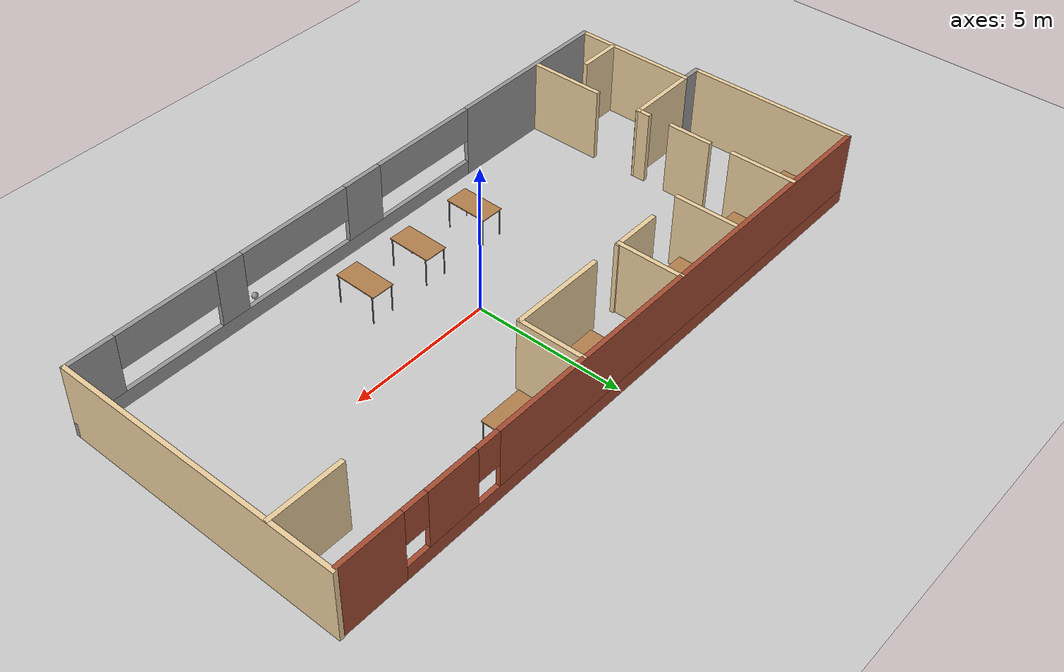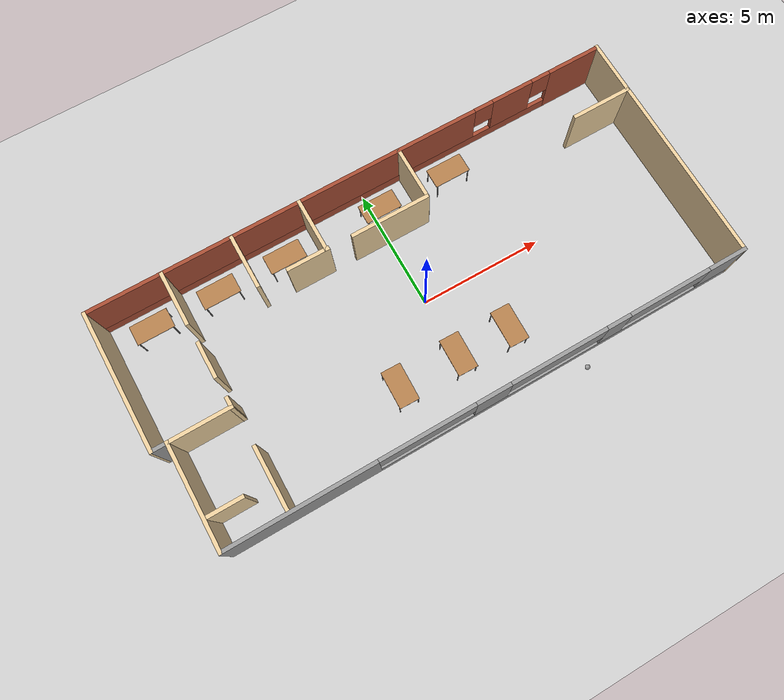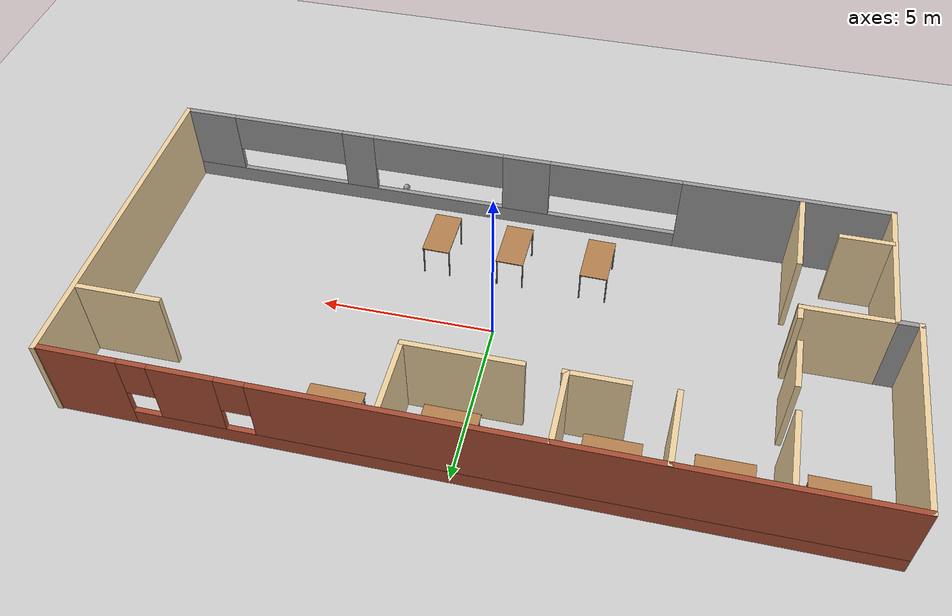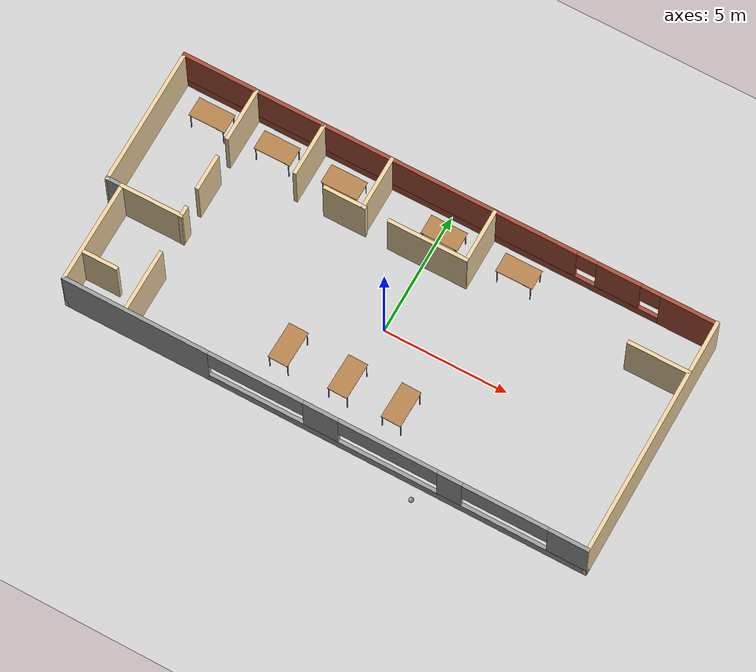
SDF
<sdf version="1.6">
 <world name="default">
  <plugin name="hello" filename="libhello.so"/>
  <light name="sun" type="directional">
   <pose>0 0 10 0 -0 0</pose>
   <diffuse>0.8 0.8 0.8 1</diffuse>
   <specular>0.2 0.2 0.2 1</specular>
   <attenuation>
    <range>1000</range>
    <constant>0.9</constant>
    <linear>0.01</linear>
    <quadratic>0.001</quadratic>
   </attenuation>
   <direction>-0.5 0.1 -0.9</direction>
  </light>
  <model name="ground_plane">
   <static>1</static>
   <link name="link">
    <collision name="collision">
     <geometry><plane><normal>0 0 1</normal><size>100 100</size></plane></geometry>
     <surface>
      <contact><collide_bitmask>65535</collide_bitmask></contact>
      <friction><ode><mu>100</mu><mu2>50</mu2></ode></friction>
     </surface>
    </collision>
    <visual name="visual">
     <cast_shadows>0</cast_shadows>
     <geometry><plane><normal>0 0 1</normal><size>100 100</size></plane></geometry>
     <material>
      <script><uri>file://media/materials/scripts/gazebo.material</uri><name>Gazebo/Grey</name></script>
     </material>
    </visual>
   </link>
  </model>
  <gravity>0 0 -9.8</gravity>
  <magnetic_field>6e-06 2.3e-05 -4.2e-05</magnetic_field>
  <atmosphere type="adiabatic"/>
  <physics name="default_physics" default="0" type="ode">
   <max_step_size>0.001</max_step_size>
   <real_time_factor>1</real_time_factor>
   <real_time_update_rate>1000</real_time_update_rate>
  </physics>
  <scene><ambient>0.4 0.4 0.4 1</ambient><background>0.7 0.7 0.7 1</background><shadows>1</shadows></scene>
  <spherical_coordinates>
   <surface_model>EARTH_WGS84</surface_model>
   <latitude_deg>0</latitude_deg>
   <longitude_deg>0</longitude_deg>
   <elevation>0</elevation>
   <heading_deg>0</heading_deg>
  </spherical_coordinates>
  <model name="my_ball">
   <link name="link_0">
    <inertial>
     <mass>1</mass>
     <inertia><ixx>0.1</ixx><ixy>0</ixy><ixz>0</ixz><iyy>0.1</iyy><iyz>0</iyz><izz>0.1</izz></inertia>
    </inertial>
    <visual name="visual">
     <geometry><sphere><radius>0.1</radius></sphere></geometry>
     <material>
      <lighting>1</lighting>
      <script><uri>file://media/materials/scripts/gazebo.material</uri><name>Gazebo/Grey</name></script>
      <shader type="pixel"><normal_map>__default__</normal_map></shader>
      <ambient>1 1 1 1</ambient>
      <diffuse>1 1 1 1</diffuse>
      <specular>1 1 1 1</specular>
      <emissive>1 1 1 1</emissive>
     </material>
    </visual>
    <collision name="collision">
     <geometry><sphere><radius>0.1</radius></sphere></geometry>
     <surface>
      <friction>
       <ode><mu>1</mu><mu2>1</mu2><fdir1>0 0 0</fdir1><slip1>0</slip1><slip2>0</slip2></ode>
       <torsional>
        <coefficient>1</coefficient>
        <patch_radius>0</patch_radius>
        <surface_radius>0</surface_radius>
        <use_patch_radius>1</use_patch_radius>
        <ode><slip>0</slip></ode>
       </torsional>
      </friction>
      <bounce><restitution_coefficient>0</restitution_coefficient><threshold>1e+06</threshold></bounce>
      <contact>
       <collide_without_contact>0</collide_without_contact>
       <collide_without_contact_bitmask>1</collide_without_contact_bitmask>
       <collide_bitmask>1</collide_bitmask>
       <ode>
        <soft_cfm>0</soft_cfm>
        <soft_erp>0.2</soft_erp>
        <kp>1e+13</kp>
        <kd>1</kd>
        <max_vel>0.01</max_vel>
        <min_depth>0</min_depth>
       </ode>
       <bullet>
        <split_impulse>1</split_impulse>
        <split_impulse_penetration_threshold>-0.01</split_impulse_penetration_threshold>
        <soft_cfm>0</soft_cfm>
        <soft_erp>0.2</soft_erp>
        <kp>1e+13</kp>
        <kd>1</kd>
       </bullet>
      </contact>
     </surface>
    </collision>
   </link>
   <static>0</static>
   <pose>3.9831 -5.22616 0.1 0 -0 0</pose>
  </model>
  <model name="table">
   <static>1</static>
   <link name="link">
    <collision name="surface">
     <pose>0 0 1 0 -0 0</pose>
     <geometry><box><size>1.5 0.8 0.03</size></box></geometry>
     <surface><friction><ode><mu>0.6</mu><mu2>0.6</mu2></ode></friction></surface>
    </collision>
    <visual name="visual1">
     <pose>0 0 1 0 -0 0</pose>
     <geometry><box><size>1.5 0.8 0.03</size></box></geometry>
     <material>
      <script><uri>file://media/materials/scripts/gazebo.material</uri><name>Gazebo/Wood</name></script>
     </material>
    </visual>
    <collision name="front_left_leg">
     <pose>0.68 0.38 0.5 0 -0 0</pose>
     <geometry><cylinder><radius>0.02</radius><length>1</length></cylinder></geometry>
    </collision>
    <visual name="front_left_leg">
     <pose>0.68 0.38 0.5 0 -0 0</pose>
     <geometry><cylinder><radius>0.02</radius><length>1</length></cylinder></geometry>
     <material>
      <script><uri>file://media/materials/scripts/gazebo.material</uri><name>Gazebo/Grey</name></script>
     </material>
    </visual>
    <collision name="front_right_leg">
     <pose>0.68 -0.38 0.5 0 -0 0</pose>
     <geometry><cylinder><radius>0.02</radius><length>1</length></cylinder></geometry>
    </collision>
    <visual name="front_right_leg">
     <pose>0.68 -0.38 0.5 0 -0 0</pose>
     <geometry><cylinder><radius>0.02</radius><length>1</length></cylinder></geometry>
     <material>
      <script><uri>file://media/materials/scripts/gazebo.material</uri><name>Gazebo/Grey</name></script>
     </material>
    </visual>
    <collision name="back_right_leg">
     <pose>-0.68 -0.38 0.5 0 -0 0</pose>
     <geometry><cylinder><radius>0.02</radius><length>1</length></cylinder></geometry>
    </collision>
    <visual name="back_right_leg">
     <pose>-0.68 -0.38 0.5 0 -0 0</pose>
     <geometry><cylinder><radius>0.02</radius><length>1</length></cylinder></geometry>
     <material>
      <script><uri>file://media/materials/scripts/gazebo.material</uri><name>Gazebo/Grey</name></script>
     </material>
    </visual>
    <collision name="back_left_leg">
     <pose>-0.68 0.38 0.5 0 -0 0</pose>
     <geometry><cylinder><radius>0.02</radius><length>1</length></cylinder></geometry>
    </collision>
    <visual name="back_left_leg">
     <pose>-0.68 0.38 0.5 0 -0 0</pose>
     <geometry><cylinder><radius>0.02</radius><length>1</length></cylinder></geometry>
     <material>
      <script><uri>file://media/materials/scripts/gazebo.material</uri><name>Gazebo/Grey</name></script>
     </material>
    </visual>
   </link>
   <pose>-2.53394 -2.50063 0 0 0 -1.59061</pose>
  </model>
  <model name="table_clone">
   <static>1</static>
   <link name="link">
    <collision name="surface">
     <pose>0 0 1 0 -0 0</pose>
     <geometry><box><size>1.5 0.8 0.03</size></box></geometry>
     <surface><friction><ode><mu>0.6</mu><mu2>0.6</mu2></ode></friction></surface>
    </collision>
    <visual name="visual1">
     <pose>0 0 1 0 -0 0</pose>
     <geometry><box><size>1.5 0.8 0.03</size></box></geometry>
     <material>
      <script><uri>file://media/materials/scripts/gazebo.material</uri><name>Gazebo/Wood</name></script>
     </material>
    </visual>
    <collision name="front_left_leg">
     <pose>0.68 0.38 0.5 0 -0 0</pose>
     <geometry><cylinder><radius>0.02</radius><length>1</length></cylinder></geometry>
    </collision>
    <visual name="front_left_leg">
     <pose>0.68 0.38 0.5 0 -0 0</pose>
     <geometry><cylinder><radius>0.02</radius><length>1</length></cylinder></geometry>
     <material>
      <script><uri>file://media/materials/scripts/gazebo.material</uri><name>Gazebo/Grey</name></script>
     </material>
    </visual>
    <collision name="front_right_leg">
     <pose>0.68 -0.38 0.5 0 -0 0</pose>
     <geometry><cylinder><radius>0.02</radius><length>1</length></cylinder></geometry>
    </collision>
    <visual name="front_right_leg">
     <pose>0.68 -0.38 0.5 0 -0 0</pose>
     <geometry><cylinder><radius>0.02</radius><length>1</length></cylinder></geometry>
     <material>
      <script><uri>file://media/materials/scripts/gazebo.material</uri><name>Gazebo/Grey</name></script>
     </material>
    </visual>
    <collision name="back_right_leg">
     <pose>-0.68 -0.38 0.5 0 -0 0</pose>
     <geometry><cylinder><radius>0.02</radius><length>1</length></cylinder></geometry>
    </collision>
    <visual name="back_right_leg">
     <pose>-0.68 -0.38 0.5 0 -0 0</pose>
     <geometry><cylinder><radius>0.02</radius><length>1</length></cylinder></geometry>
     <material>
      <script><uri>file://media/materials/scripts/gazebo.material</uri><name>Gazebo/Grey</name></script>
     </material>
    </visual>
    <collision name="back_left_leg">
     <pose>-0.68 0.38 0.5 0 -0 0</pose>
     <geometry><cylinder><radius>0.02</radius><length>1</length></cylinder></geometry>
    </collision>
    <visual name="back_left_leg">
     <pose>-0.68 0.38 0.5 0 -0 0</pose>
     <geometry><cylinder><radius>0.02</radius><length>1</length></cylinder></geometry>
     <material>
      <script><uri>file://media/materials/scripts/gazebo.material</uri><name>Gazebo/Grey</name></script>
     </material>
    </visual>
   </link>
   <pose>-0.089627 -2.52927 0 0 0 -1.59061</pose>
  </model>
  <model name="table_clone_clone">
   <static>1</static>
   <link name="link">
    <collision name="surface">
     <pose>0 0 1 0 -0 0</pose>
     <geometry><box><size>1.5 0.8 0.03</size></box></geometry>
     <surface><friction><ode><mu>0.6</mu><mu2>0.6</mu2></ode></friction></surface>
    </collision>
    <visual name="visual1">
     <pose>0 0 1 0 -0 0</pose>
     <geometry><box><size>1.5 0.8 0.03</size></box></geometry>
     <material>
      <script><uri>file://media/materials/scripts/gazebo.material</uri><name>Gazebo/Wood</name></script>
     </material>
    </visual>
    <collision name="front_left_leg">
     <pose>0.68 0.38 0.5 0 -0 0</pose>
     <geometry><cylinder><radius>0.02</radius><length>1</length></cylinder></geometry>
    </collision>
    <visual name="front_left_leg">
     <pose>0.68 0.38 0.5 0 -0 0</pose>
     <geometry><cylinder><radius>0.02</radius><length>1</length></cylinder></geometry>
     <material>
      <script><uri>file://media/materials/scripts/gazebo.material</uri><name>Gazebo/Grey</name></script>
     </material>
    </visual>
    <collision name="front_right_leg">
     <pose>0.68 -0.38 0.5 0 -0 0</pose>
     <geometry><cylinder><radius>0.02</radius><length>1</length></cylinder></geometry>
    </collision>
    <visual name="front_right_leg">
     <pose>0.68 -0.38 0.5 0 -0 0</pose>
     <geometry><cylinder><radius>0.02</radius><length>1</length></cylinder></geometry>
     <material>
      <script><uri>file://media/materials/scripts/gazebo.material</uri><name>Gazebo/Grey</name></script>
     </material>
    </visual>
    <collision name="back_right_leg">
     <pose>-0.68 -0.38 0.5 0 -0 0</pose>
     <geometry><cylinder><radius>0.02</radius><length>1</length></cylinder></geometry>
    </collision>
    <visual name="back_right_leg">
     <pose>-0.68 -0.38 0.5 0 -0 0</pose>
     <geometry><cylinder><radius>0.02</radius><length>1</length></cylinder></geometry>
     <material>
      <script><uri>file://media/materials/scripts/gazebo.material</uri><name>Gazebo/Grey</name></script>
     </material>
    </visual>
    <collision name="back_left_leg">
     <pose>-0.68 0.38 0.5 0 -0 0</pose>
     <geometry><cylinder><radius>0.02</radius><length>1</length></cylinder></geometry>
    </collision>
    <visual name="back_left_leg">
     <pose>-0.68 0.38 0.5 0 -0 0</pose>
     <geometry><cylinder><radius>0.02</radius><length>1</length></cylinder></geometry>
     <material>
      <script><uri>file://media/materials/scripts/gazebo.material</uri><name>Gazebo/Grey</name></script>
     </material>
    </visual>
   </link>
   <pose>2.09555 -2.54809 0 0 0 -1.59061</pose>
  </model>
  <model name="table_0">
   <static>1</static>
   <link name="link">
    <collision name="surface">
     <pose>0 0 1 0 -0 0</pose>
     <geometry><box><size>1.5 0.8 0.03</size></box></geometry>
     <surface><friction><ode><mu>0.6</mu><mu2>0.6</mu2></ode></friction></surface>
    </collision>
    <visual name="visual1">
     <pose>0 0 1 0 -0 0</pose>
     <geometry><box><size>1.5 0.8 0.03</size></box></geometry>
     <material>
      <script><uri>file://media/materials/scripts/gazebo.material</uri><name>Gazebo/Wood</name></script>
     </material>
    </visual>
    <collision name="front_left_leg">
     <pose>0.68 0.38 0.5 0 -0 0</pose>
     <geometry><cylinder><radius>0.02</radius><length>1</length></cylinder></geometry>
    </collision>
    <visual name="front_left_leg">
     <pose>0.68 0.38 0.5 0 -0 0</pose>
     <geometry><cylinder><radius>0.02</radius><length>1</length></cylinder></geometry>
     <material>
      <script><uri>file://media/materials/scripts/gazebo.material</uri><name>Gazebo/Grey</name></script>
     </material>
    </visual>
    <collision name="front_right_leg">
     <pose>0.68 -0.38 0.5 0 -0 0</pose>
     <geometry><cylinder><radius>0.02</radius><length>1</length></cylinder></geometry>
    </collision>
    <visual name="front_right_leg">
     <pose>0.68 -0.38 0.5 0 -0 0</pose>
     <geometry><cylinder><radius>0.02</radius><length>1</length></cylinder></geometry>
     <material>
      <script><uri>file://media/materials/scripts/gazebo.material</uri><name>Gazebo/Grey</name></script>
     </material>
    </visual>
    <collision name="back_right_leg">
     <pose>-0.68 -0.38 0.5 0 -0 0</pose>
     <geometry><cylinder><radius>0.02</radius><length>1</length></cylinder></geometry>
    </collision>
    <visual name="back_right_leg">
     <pose>-0.68 -0.38 0.5 0 -0 0</pose>
     <geometry><cylinder><radius>0.02</radius><length>1</length></cylinder></geometry>
     <material>
      <script><uri>file://media/materials/scripts/gazebo.material</uri><name>Gazebo/Grey</name></script>
     </material>
    </visual>
    <collision name="back_left_leg">
     <pose>-0.68 0.38 0.5 0 -0 0</pose>
     <geometry><cylinder><radius>0.02</radius><length>1</length></cylinder></geometry>
    </collision>
    <visual name="back_left_leg">
     <pose>-0.68 0.38 0.5 0 -0 0</pose>
     <geometry><cylinder><radius>0.02</radius><length>1</length></cylinder></geometry>
     <material>
      <script><uri>file://media/materials/scripts/gazebo.material</uri><name>Gazebo/Grey</name></script>
     </material>
    </visual>
   </link>
   <pose>0.246833 3.99529 0 0 -0 0</pose>
  </model>
  <model name="table_1">
   <static>1</static>
   <link name="link">
    <collision name="surface">
     <pose>0 0 1 0 -0 0</pose>
     <geometry><box><size>1.5 0.8 0.03</size></box></geometry>
     <surface><friction><ode><mu>0.6</mu><mu2>0.6</mu2></ode></friction></surface>
    </collision>
    <visual name="visual1">
     <pose>0 0 1 0 -0 0</pose>
     <geometry><box><size>1.5 0.8 0.03</size></box></geometry>
     <material>
      <script><uri>file://media/materials/scripts/gazebo.material</uri><name>Gazebo/Wood</name></script>
     </material>
    </visual>
    <collision name="front_left_leg">
     <pose>0.68 0.38 0.5 0 -0 0</pose>
     <geometry><cylinder><radius>0.02</radius><length>1</length></cylinder></geometry>
    </collision>
    <visual name="front_left_leg">
     <pose>0.68 0.38 0.5 0 -0 0</pose>
     <geometry><cylinder><radius>0.02</radius><length>1</length></cylinder></geometry>
     <material>
      <script><uri>file://media/materials/scripts/gazebo.material</uri><name>Gazebo/Grey</name></script>
     </material>
    </visual>
    <collision name="front_right_leg">
     <pose>0.68 -0.38 0.5 0 -0 0</pose>
     <geometry><cylinder><radius>0.02</radius><length>1</length></cylinder></geometry>
    </collision>
    <visual name="front_right_leg">
     <pose>0.68 -0.38 0.5 0 -0 0</pose>
     <geometry><cylinder><radius>0.02</radius><length>1</length></cylinder></geometry>
     <material>
      <script><uri>file://media/materials/scripts/gazebo.material</uri><name>Gazebo/Grey</name></script>
     </material>
    </visual>
    <collision name="back_right_leg">
     <pose>-0.68 -0.38 0.5 0 -0 0</pose>
     <geometry><cylinder><radius>0.02</radius><length>1</length></cylinder></geometry>
    </collision>
    <visual name="back_right_leg">
     <pose>-0.68 -0.38 0.5 0 -0 0</pose>
     <geometry><cylinder><radius>0.02</radius><length>1</length></cylinder></geometry>
     <material>
      <script><uri>file://media/materials/scripts/gazebo.material</uri><name>Gazebo/Grey</name></script>
     </material>
    </visual>
    <collision name="back_left_leg">
     <pose>-0.68 0.38 0.5 0 -0 0</pose>
     <geometry><cylinder><radius>0.02</radius><length>1</length></cylinder></geometry>
    </collision>
    <visual name="back_left_leg">
     <pose>-0.68 0.38 0.5 0 -0 0</pose>
     <geometry><cylinder><radius>0.02</radius><length>1</length></cylinder></geometry>
     <material>
      <script><uri>file://media/materials/scripts/gazebo.material</uri><name>Gazebo/Grey</name></script>
     </material>
    </visual>
   </link>
   <pose>3.30657 3.99564 0 0 -0 0</pose>
  </model>
  <model name="table_2">
   <static>1</static>
   <link name="link">
    <collision name="surface">
     <pose>0 0 1 0 -0 0</pose>
     <geometry><box><size>1.5 0.8 0.03</size></box></geometry>
     <surface><friction><ode><mu>0.6</mu><mu2>0.6</mu2></ode></friction></surface>
    </collision>
    <visual name="visual1">
     <pose>0 0 1 0 -0 0</pose>
     <geometry><box><size>1.5 0.8 0.03</size></box></geometry>
     <material>
      <script><uri>file://media/materials/scripts/gazebo.material</uri><name>Gazebo/Wood</name></script>
     </material>
    </visual>
    <collision name="front_left_leg">
     <pose>0.68 0.38 0.5 0 -0 0</pose>
     <geometry><cylinder><radius>0.02</radius><length>1</length></cylinder></geometry>
    </collision>
    <visual name="front_left_leg">
     <pose>0.68 0.38 0.5 0 -0 0</pose>
     <geometry><cylinder><radius>0.02</radius><length>1</length></cylinder></geometry>
     <material>
      <script><uri>file://media/materials/scripts/gazebo.material</uri><name>Gazebo/Grey</name></script>
     </material>
    </visual>
    <collision name="front_right_leg">
     <pose>0.68 -0.38 0.5 0 -0 0</pose>
     <geometry><cylinder><radius>0.02</radius><length>1</length></cylinder></geometry>
    </collision>
    <visual name="front_right_leg">
     <pose>0.68 -0.38 0.5 0 -0 0</pose>
     <geometry><cylinder><radius>0.02</radius><length>1</length></cylinder></geometry>
     <material>
      <script><uri>file://media/materials/scripts/gazebo.material</uri><name>Gazebo/Grey</name></script>
     </material>
    </visual>
    <collision name="back_right_leg">
     <pose>-0.68 -0.38 0.5 0 -0 0</pose>
     <geometry><cylinder><radius>0.02</radius><length>1</length></cylinder></geometry>
    </collision>
    <visual name="back_right_leg">
     <pose>-0.68 -0.38 0.5 0 -0 0</pose>
     <geometry><cylinder><radius>0.02</radius><length>1</length></cylinder></geometry>
     <material>
      <script><uri>file://media/materials/scripts/gazebo.material</uri><name>Gazebo/Grey</name></script>
     </material>
    </visual>
    <collision name="back_left_leg">
     <pose>-0.68 0.38 0.5 0 -0 0</pose>
     <geometry><cylinder><radius>0.02</radius><length>1</length></cylinder></geometry>
    </collision>
    <visual name="back_left_leg">
     <pose>-0.68 0.38 0.5 0 -0 0</pose>
     <geometry><cylinder><radius>0.02</radius><length>1</length></cylinder></geometry>
     <material>
      <script><uri>file://media/materials/scripts/gazebo.material</uri><name>Gazebo/Grey</name></script>
     </material>
    </visual>
   </link>
   <pose>-6.66029 3.99449 0 0 -0 0</pose>
  </model>
  <model name="table_3">
   <static>1</static>
   <link name="link">
    <collision name="surface">
     <pose>0 0 1 0 -0 0</pose>
     <geometry><box><size>1.5 0.8 0.03</size></box></geometry>
     <surface><friction><ode><mu>0.6</mu><mu2>0.6</mu2></ode></friction></surface>
    </collision>
    <visual name="visual1">
     <pose>0 0 1 0 -0 0</pose>
     <geometry><box><size>1.5 0.8 0.03</size></box></geometry>
     <material>
      <script><uri>file://media/materials/scripts/gazebo.material</uri><name>Gazebo/Wood</name></script>
     </material>
    </visual>
    <collision name="front_left_leg">
     <pose>0.68 0.38 0.5 0 -0 0</pose>
     <geometry><cylinder><radius>0.02</radius><length>1</length></cylinder></geometry>
    </collision>
    <visual name="front_left_leg">
     <pose>0.68 0.38 0.5 0 -0 0</pose>
     <geometry><cylinder><radius>0.02</radius><length>1</length></cylinder></geometry>
     <material>
      <script><uri>file://media/materials/scripts/gazebo.material</uri><name>Gazebo/Grey</name></script>
     </material>
    </visual>
    <collision name="front_right_leg">
     <pose>0.68 -0.38 0.5 0 -0 0</pose>
     <geometry><cylinder><radius>0.02</radius><length>1</length></cylinder></geometry>
    </collision>
    <visual name="front_right_leg">
     <pose>0.68 -0.38 0.5 0 -0 0</pose>
     <geometry><cylinder><radius>0.02</radius><length>1</length></cylinder></geometry>
     <material>
      <script><uri>file://media/materials/scripts/gazebo.material</uri><name>Gazebo/Grey</name></script>
     </material>
    </visual>
    <collision name="back_right_leg">
     <pose>-0.68 -0.38 0.5 0 -0 0</pose>
     <geometry><cylinder><radius>0.02</radius><length>1</length></cylinder></geometry>
    </collision>
    <visual name="back_right_leg">
     <pose>-0.68 -0.38 0.5 0 -0 0</pose>
     <geometry><cylinder><radius>0.02</radius><length>1</length></cylinder></geometry>
     <material>
      <script><uri>file://media/materials/scripts/gazebo.material</uri><name>Gazebo/Grey</name></script>
     </material>
    </visual>
    <collision name="back_left_leg">
     <pose>-0.68 0.38 0.5 0 -0 0</pose>
     <geometry><cylinder><radius>0.02</radius><length>1</length></cylinder></geometry>
    </collision>
    <visual name="back_left_leg">
     <pose>-0.68 0.38 0.5 0 -0 0</pose>
     <geometry><cylinder><radius>0.02</radius><length>1</length></cylinder></geometry>
     <material>
      <script><uri>file://media/materials/scripts/gazebo.material</uri><name>Gazebo/Grey</name></script>
     </material>
    </visual>
   </link>
   <pose>-3.87321 3.99481 0 0 -0 0</pose>
  </model>
  <model name="table_4">
   <static>1</static>
   <link name="link">
    <collision name="surface">
     <pose>0 0 1 0 -0 0</pose>
     <geometry><box><size>1.5 0.8 0.03</size></box></geometry>
     <surface><friction><ode><mu>0.6</mu><mu2>0.6</mu2></ode></friction></surface>
    </collision>
    <visual name="visual1">
     <pose>0 0 1 0 -0 0</pose>
     <geometry><box><size>1.5 0.8 0.03</size></box></geometry>
     <material>
      <script><uri>file://media/materials/scripts/gazebo.material</uri><name>Gazebo/Wood</name></script>
     </material>
    </visual>
    <collision name="front_left_leg">
     <pose>0.68 0.38 0.5 0 -0 0</pose>
     <geometry><cylinder><radius>0.02</radius><length>1</length></cylinder></geometry>
    </collision>
    <visual name="front_left_leg">
     <pose>0.68 0.38 0.5 0 -0 0</pose>
     <geometry><cylinder><radius>0.02</radius><length>1</length></cylinder></geometry>
     <material>
      <script><uri>file://media/materials/scripts/gazebo.material</uri><name>Gazebo/Grey</name></script>
     </material>
    </visual>
    <collision name="front_right_leg">
     <pose>0.68 -0.38 0.5 0 -0 0</pose>
     <geometry><cylinder><radius>0.02</radius><length>1</length></cylinder></geometry>
    </collision>
    <visual name="front_right_leg">
     <pose>0.68 -0.38 0.5 0 -0 0</pose>
     <geometry><cylinder><radius>0.02</radius><length>1</length></cylinder></geometry>
     <material>
      <script><uri>file://media/materials/scripts/gazebo.material</uri><name>Gazebo/Grey</name></script>
     </material>
    </visual>
    <collision name="back_right_leg">
     <pose>-0.68 -0.38 0.5 0 -0 0</pose>
     <geometry><cylinder><radius>0.02</radius><length>1</length></cylinder></geometry>
    </collision>
    <visual name="back_right_leg">
     <pose>-0.68 -0.38 0.5 0 -0 0</pose>
     <geometry><cylinder><radius>0.02</radius><length>1</length></cylinder></geometry>
     <material>
      <script><uri>file://media/materials/scripts/gazebo.material</uri><name>Gazebo/Grey</name></script>
     </material>
    </visual>
    <collision name="back_left_leg">
     <pose>-0.68 0.38 0.5 0 -0 0</pose>
     <geometry><cylinder><radius>0.02</radius><length>1</length></cylinder></geometry>
    </collision>
    <visual name="back_left_leg">
     <pose>-0.68 0.38 0.5 0 -0 0</pose>
     <geometry><cylinder><radius>0.02</radius><length>1</length></cylinder></geometry>
     <material>
      <script><uri>file://media/materials/scripts/gazebo.material</uri><name>Gazebo/Grey</name></script>
     </material>
    </visual>
   </link>
   <pose>-9.38679 3.99418 0 0 -0 0</pose>
  </model>
  <model name="structureP1">
   <link name="Wall_0">
    <pose>-0.049796 4.83077 0 0 -0 3.14159</pose>
    <visual name="Wall_0_Visual_0">
     <pose>-9.78293 0 1.25 0 -0 0</pose>
     <geometry><box><size>2.18414 0.15 2.5</size></box></geometry>
     <material>
      <script><uri>file://media/materials/scripts/gazebo.material</uri><name>Gazebo/Bricks</name></script>
      <ambient>1 1 1 1</ambient>
      <shader type="pixel"/>
      <diffuse>1 1 1 1</diffuse>
      <specular>0.2 0.2 0.2 1</specular>
      <emissive>0 0 0 1</emissive>
     </material>
     <meta><layer>0</layer></meta>
    </visual>
    <visual name="Wall_0_Visual_1">
     <pose>1.09207 0 0.25 0 -0 0</pose>
     <geometry><box><size>19.5659 0.15 0.5</size></box></geometry>
     <material>
      <script><uri>file://media/materials/scripts/gazebo.material</uri><name>Gazebo/Bricks</name></script>
      <ambient>1 1 1 1</ambient>
      <shader type="pixel"/>
      <diffuse>1 1 1 1</diffuse>
      <specular>0.2 0.2 0.2 1</specular>
      <emissive>0 0 0 1</emissive>
     </material>
     <meta><layer>0</layer></meta>
    </visual>
    <visual name="Wall_0_Visual_2">
     <pose>-7.00793 0 1.5 0 -0 0</pose>
     <geometry><box><size>1.76586 0.15 2</size></box></geometry>
     <material>
      <script><uri>file://media/materials/scripts/gazebo.material</uri><name>Gazebo/Bricks</name></script>
      <ambient>1 1 1 1</ambient>
      <shader type="pixel"/>
      <diffuse>1 1 1 1</diffuse>
      <specular>0.2 0.2 0.2 1</specular>
      <emissive>0 0 0 1</emissive>
     </material>
     <meta><layer>0</layer></meta>
    </visual>
    <visual name="Wall_0_Visual_3">
     <pose>2.775 0 1.5 0 -0 0</pose>
     <geometry><box><size>16.2 0.15 2</size></box></geometry>
     <material>
      <script><uri>file://media/materials/scripts/gazebo.material</uri><name>Gazebo/Bricks</name></script>
      <ambient>1 1 1 1</ambient>
      <shader type="pixel"/>
      <diffuse>1 1 1 1</diffuse>
      <specular>0.2 0.2 0.2 1</specular>
      <emissive>0 0 0 1</emissive>
     </material>
     <meta><layer>0</layer></meta>
    </visual>
    <visual name="Wall_0_Visual_4">
     <pose>-8.29086 0 1.9 0 -0 0</pose>
     <geometry><box><size>0.8 0.15 1.2</size></box></geometry>
     <material>
      <script><uri>file://media/materials/scripts/gazebo.material</uri><name>Gazebo/Bricks</name></script>
      <ambient>1 1 1 1</ambient>
      <shader type="pixel"/>
      <diffuse>1 1 1 1</diffuse>
      <specular>0.2 0.2 0.2 1</specular>
      <emissive>0 0 0 1</emissive>
     </material>
     <meta><layer>0</layer></meta>
    </visual>
    <visual name="Wall_0_Visual_5">
     <pose>-5.72499 0 1.9 0 -0 0</pose>
     <geometry><box><size>0.8 0.15 1.2</size></box></geometry>
     <material>
      <script><uri>file://media/materials/scripts/gazebo.material</uri><name>Gazebo/Bricks</name></script>
      <ambient>1 1 1 1</ambient>
      <shader type="pixel"/>
      <diffuse>1 1 1 1</diffuse>
      <specular>0.2 0.2 0.2 1</specular>
      <emissive>0 0 0 1</emissive>
     </material>
     <meta><layer>0</layer></meta>
    </visual>
    <collision name="Wall_0_Collision_2">
     <pose>-7.00793 0 1.5 0 -0 0</pose>
     <geometry><box><size>1.76586 0.15 2</size></box></geometry>
     <surface>
      <friction>
       <ode><mu>1</mu><mu2>1</mu2><fdir1>0 0 0</fdir1><slip1>0</slip1><slip2>0</slip2></ode>
       <torsional>
        <coefficient>1</coefficient>
        <patch_radius>0</patch_radius>
        <surface_radius>0</surface_radius>
        <use_patch_radius>1</use_patch_radius>
        <ode><slip>0</slip></ode>
       </torsional>
      </friction>
      <bounce><restitution_coefficient>0</restitution_coefficient><threshold>1e+06</threshold></bounce>
      <contact>
       <collide_without_contact>0</collide_without_contact>
       <collide_without_contact_bitmask>1</collide_without_contact_bitmask>
       <collide_bitmask>1</collide_bitmask>
       <ode>
        <soft_cfm>0</soft_cfm>
        <soft_erp>0.2</soft_erp>
        <kp>1e+13</kp>
        <kd>1</kd>
        <max_vel>0.01</max_vel>
        <min_depth>0</min_depth>
       </ode>
       <bullet>
        <split_impulse>1</split_impulse>
        <split_impulse_penetration_threshold>-0.01</split_impulse_penetration_threshold>
        <soft_cfm>0</soft_cfm>
        <soft_erp>0.2</soft_erp>
        <kp>1e+13</kp>
        <kd>1</kd>
       </bullet>
      </contact>
     </surface>
    </collision>
    <collision name="Wall_0_Collision_0">
     <pose>-9.78293 0 1.25 0 -0 0</pose>
     <geometry><box><size>2.18414 0.15 2.5</size></box></geometry>
     <surface>
      <friction>
       <ode><mu>1</mu><mu2>1</mu2><fdir1>0 0 0</fdir1><slip1>0</slip1><slip2>0</slip2></ode>
       <torsional>
        <coefficient>1</coefficient>
        <patch_radius>0</patch_radius>
        <surface_radius>0</surface_radius>
        <use_patch_radius>1</use_patch_radius>
        <ode><slip>0</slip></ode>
       </torsional>
      </friction>
      <bounce><restitution_coefficient>0</restitution_coefficient><threshold>1e+06</threshold></bounce>
      <contact>
       <collide_without_contact>0</collide_without_contact>
       <collide_without_contact_bitmask>1</collide_without_contact_bitmask>
       <collide_bitmask>1</collide_bitmask>
       <ode>
        <soft_cfm>0</soft_cfm>
        <soft_erp>0.2</soft_erp>
        <kp>1e+13</kp>
        <kd>1</kd>
        <max_vel>0.01</max_vel>
        <min_depth>0</min_depth>
       </ode>
       <bullet>
        <split_impulse>1</split_impulse>
        <split_impulse_penetration_threshold>-0.01</split_impulse_penetration_threshold>
        <soft_cfm>0</soft_cfm>
        <soft_erp>0.2</soft_erp>
        <kp>1e+13</kp>
        <kd>1</kd>
       </bullet>
      </contact>
     </surface>
    </collision>
    <collision name="Wall_0_Collision_1">
     <pose>1.09207 0 0.25 0 -0 0</pose>
     <geometry><box><size>19.5659 0.15 0.5</size></box></geometry>
     <surface>
      <friction>
       <ode><mu>1</mu><mu2>1</mu2><fdir1>0 0 0</fdir1><slip1>0</slip1><slip2>0</slip2></ode>
       <torsional>
        <coefficient>1</coefficient>
        <patch_radius>0</patch_radius>
        <surface_radius>0</surface_radius>
        <use_patch_radius>1</use_patch_radius>
        <ode><slip>0</slip></ode>
       </torsional>
      </friction>
      <bounce><restitution_coefficient>0</restitution_coefficient><threshold>1e+06</threshold></bounce>
      <contact>
       <collide_without_contact>0</collide_without_contact>
       <collide_without_contact_bitmask>1</collide_without_contact_bitmask>
       <collide_bitmask>1</collide_bitmask>
       <ode>
        <soft_cfm>0</soft_cfm>
        <soft_erp>0.2</soft_erp>
        <kp>1e+13</kp>
        <kd>1</kd>
        <max_vel>0.01</max_vel>
        <min_depth>0</min_depth>
       </ode>
       <bullet>
        <split_impulse>1</split_impulse>
        <split_impulse_penetration_threshold>-0.01</split_impulse_penetration_threshold>
        <soft_cfm>0</soft_cfm>
        <soft_erp>0.2</soft_erp>
        <kp>1e+13</kp>
        <kd>1</kd>
       </bullet>
      </contact>
     </surface>
    </collision>
    <collision name="Wall_0_Collision_5">
     <pose>-5.72499 0 1.9 0 -0 0</pose>
     <geometry><box><size>0.8 0.15 1.2</size></box></geometry>
     <surface>
      <friction>
       <ode><mu>1</mu><mu2>1</mu2><fdir1>0 0 0</fdir1><slip1>0</slip1><slip2>0</slip2></ode>
       <torsional>
        <coefficient>1</coefficient>
        <patch_radius>0</patch_radius>
        <surface_radius>0</surface_radius>
        <use_patch_radius>1</use_patch_radius>
        <ode><slip>0</slip></ode>
       </torsional>
      </friction>
      <bounce><restitution_coefficient>0</restitution_coefficient><threshold>1e+06</threshold></bounce>
      <contact>
       <collide_without_contact>0</collide_without_contact>
       <collide_without_contact_bitmask>1</collide_without_contact_bitmask>
       <collide_bitmask>1</collide_bitmask>
       <ode>
        <soft_cfm>0</soft_cfm>
        <soft_erp>0.2</soft_erp>
        <kp>1e+13</kp>
        <kd>1</kd>
        <max_vel>0.01</max_vel>
        <min_depth>0</min_depth>
       </ode>
       <bullet>
        <split_impulse>1</split_impulse>
        <split_impulse_penetration_threshold>-0.01</split_impulse_penetration_threshold>
        <soft_cfm>0</soft_cfm>
        <soft_erp>0.2</soft_erp>
        <kp>1e+13</kp>
        <kd>1</kd>
       </bullet>
      </contact>
     </surface>
    </collision>
    <collision name="Wall_0_Collision_3">
     <pose>2.775 0 1.5 0 -0 0</pose>
     <geometry><box><size>16.2 0.15 2</size></box></geometry>
     <surface>
      <friction>
       <ode><mu>1</mu><mu2>1</mu2><fdir1>0 0 0</fdir1><slip1>0</slip1><slip2>0</slip2></ode>
       <torsional>
        <coefficient>1</coefficient>
        <patch_radius>0</patch_radius>
        <surface_radius>0</surface_radius>
        <use_patch_radius>1</use_patch_radius>
        <ode><slip>0</slip></ode>
       </torsional>
      </friction>
      <bounce><restitution_coefficient>0</restitution_coefficient><threshold>1e+06</threshold></bounce>
      <contact>
       <collide_without_contact>0</collide_without_contact>
       <collide_without_contact_bitmask>1</collide_without_contact_bitmask>
       <collide_bitmask>1</collide_bitmask>
       <ode>
        <soft_cfm>0</soft_cfm>
        <soft_erp>0.2</soft_erp>
        <kp>1e+13</kp>
        <kd>1</kd>
        <max_vel>0.01</max_vel>
        <min_depth>0</min_depth>
       </ode>
       <bullet>
        <split_impulse>1</split_impulse>
        <split_impulse_penetration_threshold>-0.01</split_impulse_penetration_threshold>
        <soft_cfm>0</soft_cfm>
        <soft_erp>0.2</soft_erp>
        <kp>1e+13</kp>
        <kd>1</kd>
       </bullet>
      </contact>
     </surface>
    </collision>
    <collision name="Wall_0_Collision_4">
     <pose>-8.29086 0 1.9 0 -0 0</pose>
     <geometry><box><size>0.8 0.15 1.2</size></box></geometry>
     <surface>
      <friction>
       <ode><mu>1</mu><mu2>1</mu2><fdir1>0 0 0</fdir1><slip1>0</slip1><slip2>0</slip2></ode>
       <torsional>
        <coefficient>1</coefficient>
        <patch_radius>0</patch_radius>
        <surface_radius>0</surface_radius>
        <use_patch_radius>1</use_patch_radius>
        <ode><slip>0</slip></ode>
       </torsional>
      </friction>
      <bounce><restitution_coefficient>0</restitution_coefficient><threshold>1e+06</threshold></bounce>
      <contact>
       <collide_without_contact>0</collide_without_contact>
       <collide_without_contact_bitmask>1</collide_without_contact_bitmask>
       <collide_bitmask>1</collide_bitmask>
       <ode>
        <soft_cfm>0</soft_cfm>
        <soft_erp>0.2</soft_erp>
        <kp>1e+13</kp>
        <kd>1</kd>
        <max_vel>0.01</max_vel>
        <min_depth>0</min_depth>
       </ode>
       <bullet>
        <split_impulse>1</split_impulse>
        <split_impulse_penetration_threshold>-0.01</split_impulse_penetration_threshold>
        <soft_cfm>0</soft_cfm>
        <soft_erp>0.2</soft_erp>
        <kp>1e+13</kp>
        <kd>1</kd>
       </bullet>
      </contact>
     </surface>
    </collision>
   </link>
   <link name="Wall_1">
    <pose>-10.8498 2.03077 0 0 0 -1.56533</pose>
    <visual name="Wall_1_Visual">
     <pose>0 0 1.25 0 -0 0</pose>
     <geometry><box><size>5.71967 0.15 2.5</size></box></geometry>
     <material>
      <script><uri>file://media/materials/scripts/gazebo.material</uri><name>Gazebo/Grey</name></script>
      <ambient>0.921569 0.807843 0.615686 1</ambient>
      <shader type="pixel"/>
      <diffuse>0.7 0.7 0.7 1</diffuse>
      <specular>0.01 0.01 0.01 1</specular>
      <emissive>0 0 0 1</emissive>
     </material>
     <meta><layer>0</layer></meta>
    </visual>
    <collision name="Wall_1_Collision">
     <pose>0 0 1.25 0 -0 0</pose>
     <geometry><box><size>5.71967 0.15 2.5</size></box></geometry>
     <surface>
      <friction>
       <ode><mu>1</mu><mu2>1</mu2><fdir1>0 0 0</fdir1><slip1>0</slip1><slip2>0</slip2></ode>
       <torsional>
        <coefficient>1</coefficient>
        <patch_radius>0</patch_radius>
        <surface_radius>0</surface_radius>
        <use_patch_radius>1</use_patch_radius>
        <ode><slip>0</slip></ode>
       </torsional>
      </friction>
      <bounce><restitution_coefficient>0</restitution_coefficient><threshold>1e+06</threshold></bounce>
      <contact>
       <collide_without_contact>0</collide_without_contact>
       <collide_without_contact_bitmask>1</collide_without_contact_bitmask>
       <collide_bitmask>1</collide_bitmask>
       <ode>
        <soft_cfm>0</soft_cfm>
        <soft_erp>0.2</soft_erp>
        <kp>1e+13</kp>
        <kd>1</kd>
        <max_vel>0.01</max_vel>
        <min_depth>0</min_depth>
       </ode>
       <bullet>
        <split_impulse>1</split_impulse>
        <split_impulse_penetration_threshold>-0.01</split_impulse_penetration_threshold>
        <soft_cfm>0</soft_cfm>
        <soft_erp>0.2</soft_erp>
        <kp>1e+13</kp>
        <kd>1</kd>
       </bullet>
      </contact>
     </surface>
    </collision>
   </link>
   <link name="Wall_13">
    <pose>-9.01867 -0.748904 0 0 -0 0.004206</pose>
    <visual name="Wall_13_Visual">
     <pose>0 0 1.25 0 -0 0</pose>
     <geometry><box><size>2.58183 0.15 2.5</size></box></geometry>
     <material>
      <script><uri>file://media/materials/scripts/gazebo.material</uri><name>Gazebo/Grey</name></script>
      <ambient>0.921569 0.807843 0.615686 1</ambient>
      <shader type="pixel"/>
      <diffuse>0.7 0.7 0.7 1</diffuse>
      <specular>0.01 0.01 0.01 1</specular>
      <emissive>0 0 0 1</emissive>
     </material>
     <meta><layer>0</layer></meta>
    </visual>
    <collision name="Wall_13_Collision">
     <pose>0 0 1.25 0 -0 0</pose>
     <geometry><box><size>2.58183 0.15 2.5</size></box></geometry>
     <surface>
      <friction>
       <ode><mu>1</mu><mu2>1</mu2><fdir1>0 0 0</fdir1><slip1>0</slip1><slip2>0</slip2></ode>
       <torsional>
        <coefficient>1</coefficient>
        <patch_radius>0</patch_radius>
        <surface_radius>0</surface_radius>
        <use_patch_radius>1</use_patch_radius>
        <ode><slip>0</slip></ode>
       </torsional>
      </friction>
      <bounce><restitution_coefficient>0</restitution_coefficient><threshold>1e+06</threshold></bounce>
      <contact>
       <collide_without_contact>0</collide_without_contact>
       <collide_without_contact_bitmask>1</collide_without_contact_bitmask>
       <collide_bitmask>1</collide_bitmask>
       <ode>
        <soft_cfm>0</soft_cfm>
        <soft_erp>0.2</soft_erp>
        <kp>1e+13</kp>
        <kd>1</kd>
        <max_vel>0.01</max_vel>
        <min_depth>0</min_depth>
       </ode>
       <bullet>
        <split_impulse>1</split_impulse>
        <split_impulse_penetration_threshold>-0.01</split_impulse_penetration_threshold>
        <soft_cfm>0</soft_cfm>
        <soft_erp>0.2</soft_erp>
        <kp>1e+13</kp>
        <kd>1</kd>
       </bullet>
      </contact>
     </surface>
    </collision>
   </link>
   <link name="Wall_15">
    <pose>-7.80276 -0.579018 0 0 -0 1.5708</pose>
    <visual name="Wall_15_Visual">
     <pose>0 0 1.25 0 -0 0</pose>
     <geometry><box><size>0.5 0.15 2.5</size></box></geometry>
     <material>
      <script><uri>file://media/materials/scripts/gazebo.material</uri><name>Gazebo/Grey</name></script>
      <ambient>0.921569 0.807843 0.615686 1</ambient>
      <shader type="pixel"/>
      <diffuse>0.7 0.7 0.7 1</diffuse>
      <specular>0.01 0.01 0.01 1</specular>
      <emissive>0 0 0 1</emissive>
     </material>
     <meta><layer>0</layer></meta>
    </visual>
    <collision name="Wall_15_Collision">
     <pose>0 0 1.25 0 -0 0</pose>
     <geometry><box><size>0.5 0.15 2.5</size></box></geometry>
     <surface>
      <friction>
       <ode><mu>1</mu><mu2>1</mu2><fdir1>0 0 0</fdir1><slip1>0</slip1><slip2>0</slip2></ode>
       <torsional>
        <coefficient>1</coefficient>
        <patch_radius>0</patch_radius>
        <surface_radius>0</surface_radius>
        <use_patch_radius>1</use_patch_radius>
        <ode><slip>0</slip></ode>
       </torsional>
      </friction>
      <bounce><restitution_coefficient>0</restitution_coefficient><threshold>1e+06</threshold></bounce>
      <contact>
       <collide_without_contact>0</collide_without_contact>
       <collide_without_contact_bitmask>1</collide_without_contact_bitmask>
       <collide_bitmask>1</collide_bitmask>
       <ode>
        <soft_cfm>0</soft_cfm>
        <soft_erp>0.2</soft_erp>
        <kp>1e+13</kp>
        <kd>1</kd>
        <max_vel>0.01</max_vel>
        <min_depth>0</min_depth>
       </ode>
       <bullet>
        <split_impulse>1</split_impulse>
        <split_impulse_penetration_threshold>-0.01</split_impulse_penetration_threshold>
        <soft_cfm>0</soft_cfm>
        <soft_erp>0.2</soft_erp>
        <kp>1e+13</kp>
        <kd>1</kd>
       </bullet>
      </contact>
     </surface>
    </collision>
   </link>
   <link name="Wall_17">
    <pose>-7.82409 1.16553 0 0 -0 1.5708</pose>
    <visual name="Wall_17_Visual">
     <pose>0 0 1.25 0 -0 0</pose>
     <geometry><box><size>1.5 0.15 2.5</size></box></geometry>
     <material>
      <script><uri>file://media/materials/scripts/gazebo.material</uri><name>Gazebo/Grey</name></script>
      <ambient>0.921569 0.807843 0.615686 1</ambient>
      <shader type="pixel"/>
      <diffuse>0.7 0.7 0.7 1</diffuse>
      <specular>0.01 0.01 0.01 1</specular>
      <emissive>0 0 0 1</emissive>
     </material>
     <meta><layer>0</layer></meta>
    </visual>
    <collision name="Wall_17_Collision">
     <pose>0 0 1.25 0 -0 0</pose>
     <geometry><box><size>1.5 0.15 2.5</size></box></geometry>
     <surface>
      <friction>
       <ode><mu>1</mu><mu2>1</mu2><fdir1>0 0 0</fdir1><slip1>0</slip1><slip2>0</slip2></ode>
       <torsional>
        <coefficient>1</coefficient>
        <patch_radius>0</patch_radius>
        <surface_radius>0</surface_radius>
        <use_patch_radius>1</use_patch_radius>
        <ode><slip>0</slip></ode>
       </torsional>
      </friction>
      <bounce><restitution_coefficient>0</restitution_coefficient><threshold>1e+06</threshold></bounce>
      <contact>
       <collide_without_contact>0</collide_without_contact>
       <collide_without_contact_bitmask>1</collide_without_contact_bitmask>
       <collide_bitmask>1</collide_bitmask>
       <ode>
        <soft_cfm>0</soft_cfm>
        <soft_erp>0.2</soft_erp>
        <kp>1e+13</kp>
        <kd>1</kd>
        <max_vel>0.01</max_vel>
        <min_depth>0</min_depth>
       </ode>
       <bullet>
        <split_impulse>1</split_impulse>
        <split_impulse_penetration_threshold>-0.01</split_impulse_penetration_threshold>
        <soft_cfm>0</soft_cfm>
        <soft_erp>0.2</soft_erp>
        <kp>1e+13</kp>
        <kd>1</kd>
       </bullet>
      </contact>
     </surface>
    </collision>
   </link>
   <link name="Wall_19">
    <pose>-7.86075 3.75644 0 0 -0 1.5708</pose>
    <visual name="Wall_19_Visual">
     <pose>0 0 1.25 0 -0 0</pose>
     <geometry><box><size>2.25 0.15 2.5</size></box></geometry>
     <material>
      <script><uri>file://media/materials/scripts/gazebo.material</uri><name>Gazebo/Grey</name></script>
      <ambient>0.921569 0.807843 0.615686 1</ambient>
      <shader type="pixel"/>
      <diffuse>0.7 0.7 0.7 1</diffuse>
      <specular>0.01 0.01 0.01 1</specular>
      <emissive>0 0 0 1</emissive>
     </material>
     <meta><layer>0</layer></meta>
    </visual>
    <collision name="Wall_19_Collision">
     <pose>0 0 1.25 0 -0 0</pose>
     <geometry><box><size>2.25 0.15 2.5</size></box></geometry>
     <surface>
      <friction>
       <ode><mu>1</mu><mu2>1</mu2><fdir1>0 0 0</fdir1><slip1>0</slip1><slip2>0</slip2></ode>
       <torsional>
        <coefficient>1</coefficient>
        <patch_radius>0</patch_radius>
        <surface_radius>0</surface_radius>
        <use_patch_radius>1</use_patch_radius>
        <ode><slip>0</slip></ode>
       </torsional>
      </friction>
      <bounce><restitution_coefficient>0</restitution_coefficient><threshold>1e+06</threshold></bounce>
      <contact>
       <collide_without_contact>0</collide_without_contact>
       <collide_without_contact_bitmask>1</collide_without_contact_bitmask>
       <collide_bitmask>1</collide_bitmask>
       <ode>
        <soft_cfm>0</soft_cfm>
        <soft_erp>0.2</soft_erp>
        <kp>1e+13</kp>
        <kd>1</kd>
        <max_vel>0.01</max_vel>
        <min_depth>0</min_depth>
       </ode>
       <bullet>
        <split_impulse>1</split_impulse>
        <split_impulse_penetration_threshold>-0.01</split_impulse_penetration_threshold>
        <soft_cfm>0</soft_cfm>
        <soft_erp>0.2</soft_erp>
        <kp>1e+13</kp>
        <kd>1</kd>
       </bullet>
      </contact>
     </surface>
    </collision>
   </link>
   <link name="Wall_2">
    <pose>-10.5346 -0.754018 0 0 -0 0</pose>
    <visual name="Wall_2_Visual">
     <pose>0 0 1.25 0 -0 0</pose>
     <geometry><box><size>0.75 0.15 2.5</size></box></geometry>
     <material>
      <script><uri>file://media/materials/scripts/gazebo.material</uri><name>Gazebo/Grey</name></script>
      <ambient>1 1 1 1</ambient>
      <shader type="pixel"/>
      <diffuse>0.7 0.7 0.7 1</diffuse>
      <specular>0.01 0.01 0.01 1</specular>
      <emissive>0 0 0 1</emissive>
     </material>
     <meta><layer>0</layer></meta>
    </visual>
    <collision name="Wall_2_Collision">
     <pose>0 0 1.25 0 -0 0</pose>
     <geometry><box><size>0.75 0.15 2.5</size></box></geometry>
     <surface>
      <friction>
       <ode><mu>1</mu><mu2>1</mu2><fdir1>0 0 0</fdir1><slip1>0</slip1><slip2>0</slip2></ode>
       <torsional>
        <coefficient>1</coefficient>
        <patch_radius>0</patch_radius>
        <surface_radius>0</surface_radius>
        <use_patch_radius>1</use_patch_radius>
        <ode><slip>0</slip></ode>
       </torsional>
      </friction>
      <bounce><restitution_coefficient>0</restitution_coefficient><threshold>1e+06</threshold></bounce>
      <contact>
       <collide_without_contact>0</collide_without_contact>
       <collide_without_contact_bitmask>1</collide_without_contact_bitmask>
       <collide_bitmask>1</collide_bitmask>
       <ode>
        <soft_cfm>0</soft_cfm>
        <soft_erp>0.2</soft_erp>
        <kp>1e+13</kp>
        <kd>1</kd>
        <max_vel>0.01</max_vel>
        <min_depth>0</min_depth>
       </ode>
       <bullet>
        <split_impulse>1</split_impulse>
        <split_impulse_penetration_threshold>-0.01</split_impulse_penetration_threshold>
        <soft_cfm>0</soft_cfm>
        <soft_erp>0.2</soft_erp>
        <kp>1e+13</kp>
        <kd>1</kd>
       </bullet>
      </contact>
     </surface>
    </collision>
   </link>
   <link name="Wall_28">
    <pose>-3.02903 2.70644 0 0 -0 0</pose>
    <visual name="Wall_28_Visual">
     <pose>0 0 1.25 0 -0 0</pose>
     <geometry><box><size>1.75 0.15 2.5</size></box></geometry>
     <material>
      <script><uri>file://media/materials/scripts/gazebo.material</uri><name>Gazebo/Grey</name></script>
      <ambient>0.921569 0.807843 0.615686 1</ambient>
      <shader type="pixel"/>
      <diffuse>0.7 0.7 0.7 1</diffuse>
      <specular>0.01 0.01 0.01 1</specular>
      <emissive>0 0 0 1</emissive>
     </material>
     <meta><layer>0</layer></meta>
    </visual>
    <collision name="Wall_28_Collision">
     <pose>0 0 1.25 0 -0 0</pose>
     <geometry><box><size>1.75 0.15 2.5</size></box></geometry>
     <surface>
      <friction>
       <ode><mu>1</mu><mu2>1</mu2><fdir1>0 0 0</fdir1><slip1>0</slip1><slip2>0</slip2></ode>
       <torsional>
        <coefficient>1</coefficient>
        <patch_radius>0</patch_radius>
        <surface_radius>0</surface_radius>
        <use_patch_radius>1</use_patch_radius>
        <ode><slip>0</slip></ode>
       </torsional>
      </friction>
      <bounce><restitution_coefficient>0</restitution_coefficient><threshold>1e+06</threshold></bounce>
      <contact>
       <collide_without_contact>0</collide_without_contact>
       <collide_without_contact_bitmask>1</collide_without_contact_bitmask>
       <collide_bitmask>1</collide_bitmask>
       <ode>
        <soft_cfm>0</soft_cfm>
        <soft_erp>0.2</soft_erp>
        <kp>1e+13</kp>
        <kd>1</kd>
        <max_vel>0.01</max_vel>
        <min_depth>0</min_depth>
       </ode>
       <bullet>
        <split_impulse>1</split_impulse>
        <split_impulse_penetration_threshold>-0.01</split_impulse_penetration_threshold>
        <soft_cfm>0</soft_cfm>
        <soft_erp>0.2</soft_erp>
        <kp>1e+13</kp>
        <kd>1</kd>
       </bullet>
      </contact>
     </surface>
    </collision>
   </link>
   <link name="Wall_3">
    <pose>-10.2346 -2.80402 0 0 0 -1.5708</pose>
    <visual name="Wall_3_Visual">
     <pose>0 0 1.25 0 -0 0</pose>
     <geometry><box><size>4.25 0.15 2.5</size></box></geometry>
     <material>
      <script><uri>file://media/materials/scripts/gazebo.material</uri><name>Gazebo/Grey</name></script>
      <ambient>0.921569 0.807843 0.615686 1</ambient>
      <shader type="pixel"/>
      <diffuse>0.7 0.7 0.7 1</diffuse>
      <specular>0.01 0.01 0.01 1</specular>
      <emissive>0 0 0 1</emissive>
     </material>
     <meta><layer>0</layer></meta>
    </visual>
    <collision name="Wall_3_Collision">
     <pose>0 0 1.25 0 -0 0</pose>
     <geometry><box><size>4.25 0.15 2.5</size></box></geometry>
     <surface>
      <friction>
       <ode><mu>1</mu><mu2>1</mu2><fdir1>0 0 0</fdir1><slip1>0</slip1><slip2>0</slip2></ode>
       <torsional>
        <coefficient>1</coefficient>
        <patch_radius>0</patch_radius>
        <surface_radius>0</surface_radius>
        <use_patch_radius>1</use_patch_radius>
        <ode><slip>0</slip></ode>
       </torsional>
      </friction>
      <bounce><restitution_coefficient>0</restitution_coefficient><threshold>1e+06</threshold></bounce>
      <contact>
       <collide_without_contact>0</collide_without_contact>
       <collide_without_contact_bitmask>1</collide_without_contact_bitmask>
       <collide_bitmask>1</collide_bitmask>
       <ode>
        <soft_cfm>0</soft_cfm>
        <soft_erp>0.2</soft_erp>
        <kp>1e+13</kp>
        <kd>1</kd>
        <max_vel>0.01</max_vel>
        <min_depth>0</min_depth>
       </ode>
       <bullet>
        <split_impulse>1</split_impulse>
        <split_impulse_penetration_threshold>-0.01</split_impulse_penetration_threshold>
        <soft_cfm>0</soft_cfm>
        <soft_erp>0.2</soft_erp>
        <kp>1e+13</kp>
        <kd>1</kd>
       </bullet>
      </contact>
     </surface>
    </collision>
   </link>
   <link name="Wall_32">
    <pose>9.66593 2.70483 0 0 -0 0</pose>
    <visual name="Wall_32_Visual">
     <pose>0 0 1.25 0 -0 0</pose>
     <geometry><box><size>2.5 0.15 2.5</size></box></geometry>
     <material>
      <script><uri>file://media/materials/scripts/gazebo.material</uri><name>Gazebo/Grey</name></script>
      <ambient>0.921569 0.807843 0.615686 1</ambient>
      <shader type="pixel"/>
      <diffuse>0.7 0.7 0.7 1</diffuse>
      <specular>0.01 0.01 0.01 1</specular>
      <emissive>0 0 0 1</emissive>
     </material>
     <meta><layer>0</layer></meta>
    </visual>
    <collision name="Wall_32_Collision">
     <pose>0 0 1.25 0 -0 0</pose>
     <geometry><box><size>2.5 0.15 2.5</size></box></geometry>
     <surface>
      <friction>
       <ode><mu>1</mu><mu2>1</mu2><fdir1>0 0 0</fdir1><slip1>0</slip1><slip2>0</slip2></ode>
       <torsional>
        <coefficient>1</coefficient>
        <patch_radius>0</patch_radius>
        <surface_radius>0</surface_radius>
        <use_patch_radius>1</use_patch_radius>
        <ode><slip>0</slip></ode>
       </torsional>
      </friction>
      <bounce><restitution_coefficient>0</restitution_coefficient><threshold>1e+06</threshold></bounce>
      <contact>
       <collide_without_contact>0</collide_without_contact>
       <collide_without_contact_bitmask>1</collide_without_contact_bitmask>
       <collide_bitmask>1</collide_bitmask>
       <ode>
        <soft_cfm>0</soft_cfm>
        <soft_erp>0.2</soft_erp>
        <kp>1e+13</kp>
        <kd>1</kd>
        <max_vel>0.01</max_vel>
        <min_depth>0</min_depth>
       </ode>
       <bullet>
        <split_impulse>1</split_impulse>
        <split_impulse_penetration_threshold>-0.01</split_impulse_penetration_threshold>
        <soft_cfm>0</soft_cfm>
        <soft_erp>0.2</soft_erp>
        <kp>1e+13</kp>
        <kd>1</kd>
       </bullet>
      </contact>
     </surface>
    </collision>
   </link>
   <link name="Wall_39">
    <pose>0.371789 2.68623 0 0 -0 0</pose>
    <visual name="Wall_39_Visual">
     <pose>0 0 1.25 0 -0 0</pose>
     <geometry><box><size>3.25 0.15 2.5</size></box></geometry>
     <material>
      <script><uri>file://media/materials/scripts/gazebo.material</uri><name>Gazebo/Grey</name></script>
      <ambient>0.921569 0.807843 0.615686 1</ambient>
      <shader type="pixel"/>
      <diffuse>0.7 0.7 0.7 1</diffuse>
      <specular>0.01 0.01 0.01 1</specular>
      <emissive>0 0 0 1</emissive>
     </material>
     <meta><layer>0</layer></meta>
    </visual>
    <collision name="Wall_39_Collision">
     <pose>0 0 1.25 0 -0 0</pose>
     <geometry><box><size>3.25 0.15 2.5</size></box></geometry>
     <surface>
      <friction>
       <ode><mu>1</mu><mu2>1</mu2><fdir1>0 0 0</fdir1><slip1>0</slip1><slip2>0</slip2></ode>
       <torsional>
        <coefficient>1</coefficient>
        <patch_radius>0</patch_radius>
        <surface_radius>0</surface_radius>
        <use_patch_radius>1</use_patch_radius>
        <ode><slip>0</slip></ode>
       </torsional>
      </friction>
      <bounce><restitution_coefficient>0</restitution_coefficient><threshold>1e+06</threshold></bounce>
      <contact>
       <collide_without_contact>0</collide_without_contact>
       <collide_without_contact_bitmask>1</collide_without_contact_bitmask>
       <collide_bitmask>1</collide_bitmask>
       <ode>
        <soft_cfm>0</soft_cfm>
        <soft_erp>0.2</soft_erp>
        <kp>1e+13</kp>
        <kd>1</kd>
        <max_vel>0.01</max_vel>
        <min_depth>0</min_depth>
       </ode>
       <bullet>
        <split_impulse>1</split_impulse>
        <split_impulse_penetration_threshold>-0.01</split_impulse_penetration_threshold>
        <soft_cfm>0</soft_cfm>
        <soft_erp>0.2</soft_erp>
        <kp>1e+13</kp>
        <kd>1</kd>
       </bullet>
      </contact>
     </surface>
    </collision>
   </link>
   <link name="Wall_4">
    <pose>0.315413 -4.85402 0 0 -0 0</pose>
    <visual name="Wall_4_Visual_0">
     <pose>-7.63578 0 1.25 0 -0 0</pose>
     <geometry><box><size>5.97845 0.15 2.5</size></box></geometry>
     <material>
      <script><uri>file://media/materials/scripts/gazebo.material</uri><name>Gazebo/Grey</name></script>
      <ambient>1 1 1 1</ambient>
      <shader type="pixel"/>
      <diffuse>0.7 0.7 0.7 1</diffuse>
      <specular>0.01 0.01 0.01 1</specular>
      <emissive>0 0 0 1</emissive>
     </material>
     <meta><layer>0</layer></meta>
    </visual>
    <visual name="Wall_4_Visual_1">
     <pose>2.98922 0 0.25 0 -0 0</pose>
     <geometry><box><size>15.2716 0.15 0.5</size></box></geometry>
     <material>
      <script><uri>file://media/materials/scripts/gazebo.material</uri><name>Gazebo/Grey</name></script>
      <ambient>1 1 1 1</ambient>
      <shader type="pixel"/>
      <diffuse>0.7 0.7 0.7 1</diffuse>
      <specular>0.01 0.01 0.01 1</specular>
      <emissive>0 0 0 1</emissive>
     </material>
     <meta><layer>0</layer></meta>
    </visual>
    <visual name="Wall_4_Visual_2">
     <pose>-0.07985 0 1.5 0 -0 0</pose>
     <geometry><box><size>1.41641 0.15 2</size></box></geometry>
     <material>
      <script><uri>file://media/materials/scripts/gazebo.material</uri><name>Gazebo/Grey</name></script>
      <ambient>1 1 1 1</ambient>
      <shader type="pixel"/>
      <diffuse>0.7 0.7 0.7 1</diffuse>
      <specular>0.01 0.01 0.01 1</specular>
      <emissive>0 0 0 1</emissive>
     </material>
     <meta><layer>0</layer></meta>
    </visual>
    <visual name="Wall_4_Visual_3">
     <pose>5.09381 0 1.5 0 -0 0</pose>
     <geometry><box><size>0.983588 0.15 2</size></box></geometry>
     <material>
      <script><uri>file://media/materials/scripts/gazebo.material</uri><name>Gazebo/Grey</name></script>
      <ambient>1 1 1 1</ambient>
      <shader type="pixel"/>
      <diffuse>0.7 0.7 0.7 1</diffuse>
      <specular>0.01 0.01 0.01 1</specular>
      <emissive>0 0 0 1</emissive>
     </material>
     <meta><layer>0</layer></meta>
    </visual>
    <visual name="Wall_4_Visual_4">
     <pose>9.81177 0 1.5 0 -0 0</pose>
     <geometry><box><size>1.62645 0.15 2</size></box></geometry>
     <material>
      <script><uri>file://media/materials/scripts/gazebo.material</uri><name>Gazebo/Grey</name></script>
      <ambient>1 1 1 1</ambient>
      <shader type="pixel"/>
      <diffuse>0.7 0.7 0.7 1</diffuse>
      <specular>0.01 0.01 0.01 1</specular>
      <emissive>0 0 0 1</emissive>
     </material>
     <meta><layer>0</layer></meta>
    </visual>
    <visual name="Wall_4_Visual_5">
     <pose>-2.71731 0 1.9 0 -0 0</pose>
     <geometry><box><size>3.8585 0.15 1.2</size></box></geometry>
     <material>
      <script><uri>file://media/materials/scripts/gazebo.material</uri><name>Gazebo/Grey</name></script>
      <ambient>1 1 1 1</ambient>
      <shader type="pixel"/>
      <diffuse>0.7 0.7 0.7 1</diffuse>
      <specular>0.01 0.01 0.01 1</specular>
      <emissive>0 0 0 1</emissive>
     </material>
     <meta><layer>0</layer></meta>
    </visual>
    <visual name="Wall_4_Visual_6">
     <pose>2.61519 0 1.9 0 -0 0</pose>
     <geometry><box><size>3.97366 0.15 1.2</size></box></geometry>
     <material>
      <script><uri>file://media/materials/scripts/gazebo.material</uri><name>Gazebo/Grey</name></script>
      <ambient>1 1 1 1</ambient>
      <shader type="pixel"/>
      <diffuse>0.7 0.7 0.7 1</diffuse>
      <specular>0.01 0.01 0.01 1</specular>
      <emissive>0 0 0 1</emissive>
     </material>
     <meta><layer>0</layer></meta>
    </visual>
    <visual name="Wall_4_Visual_7">
     <pose>7.29208 0 1.9 0 -0 0</pose>
     <geometry><box><size>3.41294 0.15 1.2</size></box></geometry>
     <material>
      <script><uri>file://media/materials/scripts/gazebo.material</uri><name>Gazebo/Grey</name></script>
      <ambient>1 1 1 1</ambient>
      <shader type="pixel"/>
      <diffuse>0.7 0.7 0.7 1</diffuse>
      <specular>0.01 0.01 0.01 1</specular>
      <emissive>0 0 0 1</emissive>
     </material>
     <meta><layer>0</layer></meta>
    </visual>
    <collision name="Wall_4_Collision_0">
     <pose>-7.63578 0 1.25 0 -0 0</pose>
     <geometry><box><size>5.97845 0.15 2.5</size></box></geometry>
     <surface>
      <friction>
       <ode><mu>1</mu><mu2>1</mu2><fdir1>0 0 0</fdir1><slip1>0</slip1><slip2>0</slip2></ode>
       <torsional>
        <coefficient>1</coefficient>
        <patch_radius>0</patch_radius>
        <surface_radius>0</surface_radius>
        <use_patch_radius>1</use_patch_radius>
        <ode><slip>0</slip></ode>
       </torsional>
      </friction>
      <bounce><restitution_coefficient>0</restitution_coefficient><threshold>1e+06</threshold></bounce>
      <contact>
       <collide_without_contact>0</collide_without_contact>
       <collide_without_contact_bitmask>1</collide_without_contact_bitmask>
       <collide_bitmask>1</collide_bitmask>
       <ode>
        <soft_cfm>0</soft_cfm>
        <soft_erp>0.2</soft_erp>
        <kp>1e+13</kp>
        <kd>1</kd>
        <max_vel>0.01</max_vel>
        <min_depth>0</min_depth>
       </ode>
       <bullet>
        <split_impulse>1</split_impulse>
        <split_impulse_penetration_threshold>-0.01</split_impulse_penetration_threshold>
        <soft_cfm>0</soft_cfm>
        <soft_erp>0.2</soft_erp>
        <kp>1e+13</kp>
        <kd>1</kd>
       </bullet>
      </contact>
     </surface>
    </collision>
    <collision name="Wall_4_Collision_2">
     <pose>-0.07985 0 1.5 0 -0 0</pose>
     <geometry><box><size>1.41641 0.15 2</size></box></geometry>
     <surface>
      <friction>
       <ode><mu>1</mu><mu2>1</mu2><fdir1>0 0 0</fdir1><slip1>0</slip1><slip2>0</slip2></ode>
       <torsional>
        <coefficient>1</coefficient>
        <patch_radius>0</patch_radius>
        <surface_radius>0</surface_radius>
        <use_patch_radius>1</use_patch_radius>
        <ode><slip>0</slip></ode>
       </torsional>
      </friction>
      <bounce><restitution_coefficient>0</restitution_coefficient><threshold>1e+06</threshold></bounce>
      <contact>
       <collide_without_contact>0</collide_without_contact>
       <collide_without_contact_bitmask>1</collide_without_contact_bitmask>
       <collide_bitmask>1</collide_bitmask>
       <ode>
        <soft_cfm>0</soft_cfm>
        <soft_erp>0.2</soft_erp>
        <kp>1e+13</kp>
        <kd>1</kd>
        <max_vel>0.01</max_vel>
        <min_depth>0</min_depth>
       </ode>
       <bullet>
        <split_impulse>1</split_impulse>
        <split_impulse_penetration_threshold>-0.01</split_impulse_penetration_threshold>
        <soft_cfm>0</soft_cfm>
        <soft_erp>0.2</soft_erp>
        <kp>1e+13</kp>
        <kd>1</kd>
       </bullet>
      </contact>
     </surface>
    </collision>
    <collision name="Wall_4_Collision_1">
     <pose>2.98922 0 0.25 0 -0 0</pose>
     <geometry><box><size>15.2716 0.15 0.5</size></box></geometry>
     <surface>
      <friction>
       <ode><mu>1</mu><mu2>1</mu2><fdir1>0 0 0</fdir1><slip1>0</slip1><slip2>0</slip2></ode>
       <torsional>
        <coefficient>1</coefficient>
        <patch_radius>0</patch_radius>
        <surface_radius>0</surface_radius>
        <use_patch_radius>1</use_patch_radius>
        <ode><slip>0</slip></ode>
       </torsional>
      </friction>
      <bounce><restitution_coefficient>0</restitution_coefficient><threshold>1e+06</threshold></bounce>
      <contact>
       <collide_without_contact>0</collide_without_contact>
       <collide_without_contact_bitmask>1</collide_without_contact_bitmask>
       <collide_bitmask>1</collide_bitmask>
       <ode>
        <soft_cfm>0</soft_cfm>
        <soft_erp>0.2</soft_erp>
        <kp>1e+13</kp>
        <kd>1</kd>
        <max_vel>0.01</max_vel>
        <min_depth>0</min_depth>
       </ode>
       <bullet>
        <split_impulse>1</split_impulse>
        <split_impulse_penetration_threshold>-0.01</split_impulse_penetration_threshold>
        <soft_cfm>0</soft_cfm>
        <soft_erp>0.2</soft_erp>
        <kp>1e+13</kp>
        <kd>1</kd>
       </bullet>
      </contact>
     </surface>
    </collision>
    <collision name="Wall_4_Collision_3">
     <pose>5.09381 0 1.5 0 -0 0</pose>
     <geometry><box><size>0.983588 0.15 2</size></box></geometry>
     <surface>
      <friction>
       <ode><mu>1</mu><mu2>1</mu2><fdir1>0 0 0</fdir1><slip1>0</slip1><slip2>0</slip2></ode>
       <torsional>
        <coefficient>1</coefficient>
        <patch_radius>0</patch_radius>
        <surface_radius>0</surface_radius>
        <use_patch_radius>1</use_patch_radius>
        <ode><slip>0</slip></ode>
       </torsional>
      </friction>
      <bounce><restitution_coefficient>0</restitution_coefficient><threshold>1e+06</threshold></bounce>
      <contact>
       <collide_without_contact>0</collide_without_contact>
       <collide_without_contact_bitmask>1</collide_without_contact_bitmask>
       <collide_bitmask>1</collide_bitmask>
       <ode>
        <soft_cfm>0</soft_cfm>
        <soft_erp>0.2</soft_erp>
        <kp>1e+13</kp>
        <kd>1</kd>
        <max_vel>0.01</max_vel>
        <min_depth>0</min_depth>
       </ode>
       <bullet>
        <split_impulse>1</split_impulse>
        <split_impulse_penetration_threshold>-0.01</split_impulse_penetration_threshold>
        <soft_cfm>0</soft_cfm>
        <soft_erp>0.2</soft_erp>
        <kp>1e+13</kp>
        <kd>1</kd>
       </bullet>
      </contact>
     </surface>
    </collision>
    <collision name="Wall_4_Collision_4">
     <pose>9.81177 0 1.5 0 -0 0</pose>
     <geometry><box><size>1.62645 0.15 2</size></box></geometry>
     <surface>
      <friction>
       <ode><mu>1</mu><mu2>1</mu2><fdir1>0 0 0</fdir1><slip1>0</slip1><slip2>0</slip2></ode>
       <torsional>
        <coefficient>1</coefficient>
        <patch_radius>0</patch_radius>
        <surface_radius>0</surface_radius>
        <use_patch_radius>1</use_patch_radius>
        <ode><slip>0</slip></ode>
       </torsional>
      </friction>
      <bounce><restitution_coefficient>0</restitution_coefficient><threshold>1e+06</threshold></bounce>
      <contact>
       <collide_without_contact>0</collide_without_contact>
       <collide_without_contact_bitmask>1</collide_without_contact_bitmask>
       <collide_bitmask>1</collide_bitmask>
       <ode>
        <soft_cfm>0</soft_cfm>
        <soft_erp>0.2</soft_erp>
        <kp>1e+13</kp>
        <kd>1</kd>
        <max_vel>0.01</max_vel>
        <min_depth>0</min_depth>
       </ode>
       <bullet>
        <split_impulse>1</split_impulse>
        <split_impulse_penetration_threshold>-0.01</split_impulse_penetration_threshold>
        <soft_cfm>0</soft_cfm>
        <soft_erp>0.2</soft_erp>
        <kp>1e+13</kp>
        <kd>1</kd>
       </bullet>
      </contact>
     </surface>
    </collision>
    <collision name="Wall_4_Collision_6">
     <pose>2.61519 0 1.9 0 -0 0</pose>
     <geometry><box><size>3.97366 0.15 1.2</size></box></geometry>
     <surface>
      <friction>
       <ode><mu>1</mu><mu2>1</mu2><fdir1>0 0 0</fdir1><slip1>0</slip1><slip2>0</slip2></ode>
       <torsional>
        <coefficient>1</coefficient>
        <patch_radius>0</patch_radius>
        <surface_radius>0</surface_radius>
        <use_patch_radius>1</use_patch_radius>
        <ode><slip>0</slip></ode>
       </torsional>
      </friction>
      <bounce><restitution_coefficient>0</restitution_coefficient><threshold>1e+06</threshold></bounce>
      <contact>
       <collide_without_contact>0</collide_without_contact>
       <collide_without_contact_bitmask>1</collide_without_contact_bitmask>
       <collide_bitmask>1</collide_bitmask>
       <ode>
        <soft_cfm>0</soft_cfm>
        <soft_erp>0.2</soft_erp>
        <kp>1e+13</kp>
        <kd>1</kd>
        <max_vel>0.01</max_vel>
        <min_depth>0</min_depth>
       </ode>
       <bullet>
        <split_impulse>1</split_impulse>
        <split_impulse_penetration_threshold>-0.01</split_impulse_penetration_threshold>
        <soft_cfm>0</soft_cfm>
        <soft_erp>0.2</soft_erp>
        <kp>1e+13</kp>
        <kd>1</kd>
       </bullet>
      </contact>
     </surface>
    </collision>
    <collision name="Wall_4_Collision_5">
     <pose>-2.71731 0 1.9 0 -0 0</pose>
     <geometry><box><size>3.8585 0.15 1.2</size></box></geometry>
     <surface>
      <friction>
       <ode><mu>1</mu><mu2>1</mu2><fdir1>0 0 0</fdir1><slip1>0</slip1><slip2>0</slip2></ode>
       <torsional>
        <coefficient>1</coefficient>
        <patch_radius>0</patch_radius>
        <surface_radius>0</surface_radius>
        <use_patch_radius>1</use_patch_radius>
        <ode><slip>0</slip></ode>
       </torsional>
      </friction>
      <bounce><restitution_coefficient>0</restitution_coefficient><threshold>1e+06</threshold></bounce>
      <contact>
       <collide_without_contact>0</collide_without_contact>
       <collide_without_contact_bitmask>1</collide_without_contact_bitmask>
       <collide_bitmask>1</collide_bitmask>
       <ode>
        <soft_cfm>0</soft_cfm>
        <soft_erp>0.2</soft_erp>
        <kp>1e+13</kp>
        <kd>1</kd>
        <max_vel>0.01</max_vel>
        <min_depth>0</min_depth>
       </ode>
       <bullet>
        <split_impulse>1</split_impulse>
        <split_impulse_penetration_threshold>-0.01</split_impulse_penetration_threshold>
        <soft_cfm>0</soft_cfm>
        <soft_erp>0.2</soft_erp>
        <kp>1e+13</kp>
        <kd>1</kd>
       </bullet>
      </contact>
     </surface>
    </collision>
    <collision name="Wall_4_Collision_7">
     <pose>7.29208 0 1.9 0 -0 0</pose>
     <geometry><box><size>3.41294 0.15 1.2</size></box></geometry>
     <surface>
      <friction>
       <ode><mu>1</mu><mu2>1</mu2><fdir1>0 0 0</fdir1><slip1>0</slip1><slip2>0</slip2></ode>
       <torsional>
        <coefficient>1</coefficient>
        <patch_radius>0</patch_radius>
        <surface_radius>0</surface_radius>
        <use_patch_radius>1</use_patch_radius>
        <ode><slip>0</slip></ode>
       </torsional>
      </friction>
      <bounce><restitution_coefficient>0</restitution_coefficient><threshold>1e+06</threshold></bounce>
      <contact>
       <collide_without_contact>0</collide_without_contact>
       <collide_without_contact_bitmask>1</collide_without_contact_bitmask>
       <collide_bitmask>1</collide_bitmask>
       <ode>
        <soft_cfm>0</soft_cfm>
        <soft_erp>0.2</soft_erp>
        <kp>1e+13</kp>
        <kd>1</kd>
        <max_vel>0.01</max_vel>
        <min_depth>0</min_depth>
       </ode>
       <bullet>
        <split_impulse>1</split_impulse>
        <split_impulse_penetration_threshold>-0.01</split_impulse_penetration_threshold>
        <soft_cfm>0</soft_cfm>
        <soft_erp>0.2</soft_erp>
        <kp>1e+13</kp>
        <kd>1</kd>
       </bullet>
      </contact>
     </surface>
    </collision>
   </link>
   <link name="Wall_42">
    <pose>-5.06371 3.76248 0 0 0 -1.5708</pose>
    <visual name="Wall_42_Visual">
     <pose>0 0 1.25 0 -0 0</pose>
     <geometry><box><size>2.25 0.15 2.5</size></box></geometry>
     <material>
      <script><uri>file://media/materials/scripts/gazebo.material</uri><name>Gazebo/Grey</name></script>
      <ambient>0.921569 0.807843 0.615686 1</ambient>
      <shader type="pixel"/>
      <diffuse>0.7 0.7 0.7 1</diffuse>
      <specular>0.01 0.01 0.01 1</specular>
      <emissive>0 0 0 1</emissive>
     </material>
     <meta><layer>0</layer></meta>
    </visual>
    <collision name="Wall_42_Collision">
     <pose>0 0 1.25 0 -0 0</pose>
     <geometry><box><size>2.25 0.15 2.5</size></box></geometry>
     <surface>
      <friction>
       <ode><mu>1</mu><mu2>1</mu2><fdir1>0 0 0</fdir1><slip1>0</slip1><slip2>0</slip2></ode>
       <torsional>
        <coefficient>1</coefficient>
        <patch_radius>0</patch_radius>
        <surface_radius>0</surface_radius>
        <use_patch_radius>1</use_patch_radius>
        <ode><slip>0</slip></ode>
       </torsional>
      </friction>
      <bounce><restitution_coefficient>0</restitution_coefficient><threshold>1e+06</threshold></bounce>
      <contact>
       <collide_without_contact>0</collide_without_contact>
       <collide_without_contact_bitmask>1</collide_without_contact_bitmask>
       <collide_bitmask>1</collide_bitmask>
       <ode>
        <soft_cfm>0</soft_cfm>
        <soft_erp>0.2</soft_erp>
        <kp>1e+13</kp>
        <kd>1</kd>
        <max_vel>0.01</max_vel>
        <min_depth>0</min_depth>
       </ode>
       <bullet>
        <split_impulse>1</split_impulse>
        <split_impulse_penetration_threshold>-0.01</split_impulse_penetration_threshold>
        <soft_cfm>0</soft_cfm>
        <soft_erp>0.2</soft_erp>
        <kp>1e+13</kp>
        <kd>1</kd>
       </bullet>
      </contact>
     </surface>
    </collision>
   </link>
   <link name="Wall_44">
    <pose>-2.28158 3.77586 0 0 0 -1.5708</pose>
    <visual name="Wall_44_Visual">
     <pose>0 0 1.25 0 -0 0</pose>
     <geometry><box><size>2.25 0.15 2.5</size></box></geometry>
     <material>
      <script><uri>file://media/materials/scripts/gazebo.material</uri><name>Gazebo/Grey</name></script>
      <ambient>0.921569 0.807843 0.615686 1</ambient>
      <shader type="pixel"/>
      <diffuse>0.7 0.7 0.7 1</diffuse>
      <specular>0.01 0.01 0.01 1</specular>
      <emissive>0 0 0 1</emissive>
     </material>
     <meta><layer>0</layer></meta>
    </visual>
    <collision name="Wall_44_Collision">
     <pose>0 0 1.25 0 -0 0</pose>
     <geometry><box><size>2.25 0.15 2.5</size></box></geometry>
     <surface>
      <friction>
       <ode><mu>1</mu><mu2>1</mu2><fdir1>0 0 0</fdir1><slip1>0</slip1><slip2>0</slip2></ode>
       <torsional>
        <coefficient>1</coefficient>
        <patch_radius>0</patch_radius>
        <surface_radius>0</surface_radius>
        <use_patch_radius>1</use_patch_radius>
        <ode><slip>0</slip></ode>
       </torsional>
      </friction>
      <bounce><restitution_coefficient>0</restitution_coefficient><threshold>1e+06</threshold></bounce>
      <contact>
       <collide_without_contact>0</collide_without_contact>
       <collide_without_contact_bitmask>1</collide_without_contact_bitmask>
       <collide_bitmask>1</collide_bitmask>
       <ode>
        <soft_cfm>0</soft_cfm>
        <soft_erp>0.2</soft_erp>
        <kp>1e+13</kp>
        <kd>1</kd>
        <max_vel>0.01</max_vel>
        <min_depth>0</min_depth>
       </ode>
       <bullet>
        <split_impulse>1</split_impulse>
        <split_impulse_penetration_threshold>-0.01</split_impulse_penetration_threshold>
        <soft_cfm>0</soft_cfm>
        <soft_erp>0.2</soft_erp>
        <kp>1e+13</kp>
        <kd>1</kd>
       </bullet>
      </contact>
     </surface>
    </collision>
   </link>
   <link name="Wall_46">
    <pose>1.93613 3.7491 0 0 0 -1.5708</pose>
    <visual name="Wall_46_Visual">
     <pose>0 0 1.25 0 -0 0</pose>
     <geometry><box><size>2.25 0.15 2.5</size></box></geometry>
     <material>
      <script><uri>file://media/materials/scripts/gazebo.material</uri><name>Gazebo/Grey</name></script>
      <ambient>0.921569 0.807843 0.615686 1</ambient>
      <shader type="pixel"/>
      <diffuse>0.7 0.7 0.7 1</diffuse>
      <specular>0.01 0.01 0.01 1</specular>
      <emissive>0 0 0 1</emissive>
     </material>
     <meta><layer>0</layer></meta>
    </visual>
    <collision name="Wall_46_Collision">
     <pose>0 0 1.25 0 -0 0</pose>
     <geometry><box><size>2.25 0.15 2.5</size></box></geometry>
     <surface>
      <friction>
       <ode><mu>1</mu><mu2>1</mu2><fdir1>0 0 0</fdir1><slip1>0</slip1><slip2>0</slip2></ode>
       <torsional>
        <coefficient>1</coefficient>
        <patch_radius>0</patch_radius>
        <surface_radius>0</surface_radius>
        <use_patch_radius>1</use_patch_radius>
        <ode><slip>0</slip></ode>
       </torsional>
      </friction>
      <bounce><restitution_coefficient>0</restitution_coefficient><threshold>1e+06</threshold></bounce>
      <contact>
       <collide_without_contact>0</collide_without_contact>
       <collide_without_contact_bitmask>1</collide_without_contact_bitmask>
       <collide_bitmask>1</collide_bitmask>
       <ode>
        <soft_cfm>0</soft_cfm>
        <soft_erp>0.2</soft_erp>
        <kp>1e+13</kp>
        <kd>1</kd>
        <max_vel>0.01</max_vel>
        <min_depth>0</min_depth>
       </ode>
       <bullet>
        <split_impulse>1</split_impulse>
        <split_impulse_penetration_threshold>-0.01</split_impulse_penetration_threshold>
        <soft_cfm>0</soft_cfm>
        <soft_erp>0.2</soft_erp>
        <kp>1e+13</kp>
        <kd>1</kd>
       </bullet>
      </contact>
     </surface>
    </collision>
   </link>
   <link name="Wall_5">
    <pose>10.8654 0 0 0 -0 1.5708</pose>
    <visual name="Wall_5_Visual">
     <pose>0 0 1.25 0 -0 0</pose>
     <geometry><box><size>9.85804 0.15 2.5</size></box></geometry>
     <material>
      <script><uri>file://media/materials/scripts/gazebo.material</uri><name>Gazebo/Grey</name></script>
      <ambient>0.921569 0.807843 0.615686 1</ambient>
      <shader type="pixel"/>
      <diffuse>0.7 0.7 0.7 1</diffuse>
      <specular>0.01 0.01 0.01 1</specular>
      <emissive>0 0 0 1</emissive>
     </material>
     <meta><layer>0</layer></meta>
    </visual>
    <collision name="Wall_5_Collision">
     <pose>0 0 1.25 0 -0 0</pose>
     <geometry><box><size>9.85804 0.15 2.5</size></box></geometry>
     <surface>
      <friction>
       <ode><mu>1</mu><mu2>1</mu2><fdir1>0 0 0</fdir1><slip1>0</slip1><slip2>0</slip2></ode>
       <torsional>
        <coefficient>1</coefficient>
        <patch_radius>0</patch_radius>
        <surface_radius>0</surface_radius>
        <use_patch_radius>1</use_patch_radius>
        <ode><slip>0</slip></ode>
       </torsional>
      </friction>
      <bounce><restitution_coefficient>0</restitution_coefficient><threshold>1e+06</threshold></bounce>
      <contact>
       <collide_without_contact>0</collide_without_contact>
       <collide_without_contact_bitmask>1</collide_without_contact_bitmask>
       <collide_bitmask>1</collide_bitmask>
       <ode>
        <soft_cfm>0</soft_cfm>
        <soft_erp>0.2</soft_erp>
        <kp>1e+13</kp>
        <kd>1</kd>
        <max_vel>0.01</max_vel>
        <min_depth>0</min_depth>
       </ode>
       <bullet>
        <split_impulse>1</split_impulse>
        <split_impulse_penetration_threshold>-0.01</split_impulse_penetration_threshold>
        <soft_cfm>0</soft_cfm>
        <soft_erp>0.2</soft_erp>
        <kp>1e+13</kp>
        <kd>1</kd>
       </bullet>
      </contact>
     </surface>
    </collision>
   </link>
   <link name="Wall_7">
    <pose>-7.7222 -3.53861 0 0 0 -1.5708</pose>
    <visual name="Wall_7_Visual">
     <pose>0 0 1.25 0 -0 0</pose>
     <geometry><box><size>2.5 0.15 2.5</size></box></geometry>
     <material>
      <script><uri>file://media/materials/scripts/gazebo.material</uri><name>Gazebo/Grey</name></script>
      <ambient>0.921569 0.807843 0.615686 1</ambient>
      <shader type="pixel"/>
      <diffuse>0.7 0.7 0.7 1</diffuse>
      <specular>0.01 0.01 0.01 1</specular>
      <emissive>0 0 0 1</emissive>
     </material>
     <meta><layer>0</layer></meta>
    </visual>
    <collision name="Wall_7_Collision">
     <pose>0 0 1.25 0 -0 0</pose>
     <geometry><box><size>2.5 0.15 2.5</size></box></geometry>
     <surface>
      <friction>
       <ode><mu>1</mu><mu2>1</mu2><fdir1>0 0 0</fdir1><slip1>0</slip1><slip2>0</slip2></ode>
       <torsional>
        <coefficient>1</coefficient>
        <patch_radius>0</patch_radius>
        <surface_radius>0</surface_radius>
        <use_patch_radius>1</use_patch_radius>
        <ode><slip>0</slip></ode>
       </torsional>
      </friction>
      <bounce><restitution_coefficient>0</restitution_coefficient><threshold>1e+06</threshold></bounce>
      <contact>
       <collide_without_contact>0</collide_without_contact>
       <collide_without_contact_bitmask>1</collide_without_contact_bitmask>
       <collide_bitmask>1</collide_bitmask>
       <ode>
        <soft_cfm>0</soft_cfm>
        <soft_erp>0.2</soft_erp>
        <kp>1e+13</kp>
        <kd>1</kd>
        <max_vel>0.01</max_vel>
        <min_depth>0</min_depth>
       </ode>
       <bullet>
        <split_impulse>1</split_impulse>
        <split_impulse_penetration_threshold>-0.01</split_impulse_penetration_threshold>
        <soft_cfm>0</soft_cfm>
        <soft_erp>0.2</soft_erp>
        <kp>1e+13</kp>
        <kd>1</kd>
       </bullet>
      </contact>
     </surface>
    </collision>
   </link>
   <link name="Wall_9">
    <pose>-9.48851 -3.62813 0 0 -0 0</pose>
    <visual name="Wall_9_Visual">
     <pose>0 0 1.25 0 -0 0</pose>
     <geometry><box><size>1.5 0.15 2.5</size></box></geometry>
     <material>
      <script><uri>file://media/materials/scripts/gazebo.material</uri><name>Gazebo/Grey</name></script>
      <ambient>0.921569 0.807843 0.615686 1</ambient>
      <shader type="pixel"/>
      <diffuse>0.7 0.7 0.7 1</diffuse>
      <specular>0.01 0.01 0.01 1</specular>
      <emissive>0 0 0 1</emissive>
     </material>
     <meta><layer>0</layer></meta>
    </visual>
    <collision name="Wall_9_Collision">
     <pose>0 0 1.25 0 -0 0</pose>
     <geometry><box><size>1.5 0.15 2.5</size></box></geometry>
     <surface>
      <friction>
       <ode><mu>1</mu><mu2>1</mu2><fdir1>0 0 0</fdir1><slip1>0</slip1><slip2>0</slip2></ode>
       <torsional>
        <coefficient>1</coefficient>
        <patch_radius>0</patch_radius>
        <surface_radius>0</surface_radius>
        <use_patch_radius>1</use_patch_radius>
        <ode><slip>0</slip></ode>
       </torsional>
      </friction>
      <bounce><restitution_coefficient>0</restitution_coefficient><threshold>1e+06</threshold></bounce>
      <contact>
       <collide_without_contact>0</collide_without_contact>
       <collide_without_contact_bitmask>1</collide_without_contact_bitmask>
       <collide_bitmask>1</collide_bitmask>
       <ode>
        <soft_cfm>0</soft_cfm>
        <soft_erp>0.2</soft_erp>
        <kp>1e+13</kp>
        <kd>1</kd>
        <max_vel>0.01</max_vel>
        <min_depth>0</min_depth>
       </ode>
       <bullet>
        <split_impulse>1</split_impulse>
        <split_impulse_penetration_threshold>-0.01</split_impulse_penetration_threshold>
        <soft_cfm>0</soft_cfm>
        <soft_erp>0.2</soft_erp>
        <kp>1e+13</kp>
        <kd>1</kd>
       </bullet>
      </contact>
     </surface>
    </collision>
   </link>
   <static>1</static>
   <pose>-0.21444 0.223052 0 0 -0 0</pose>
  </model>
 </world>
</sdf>
